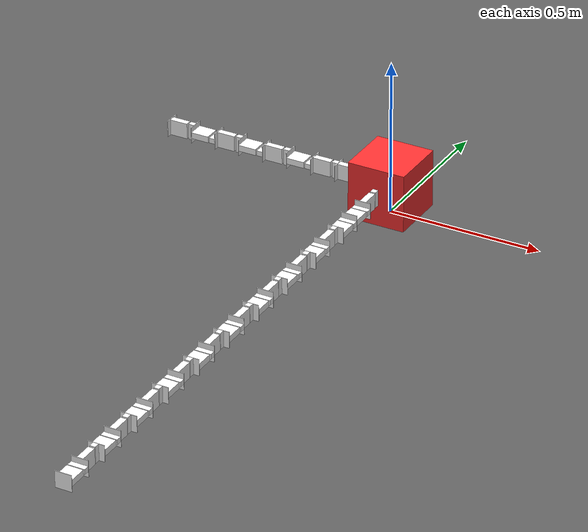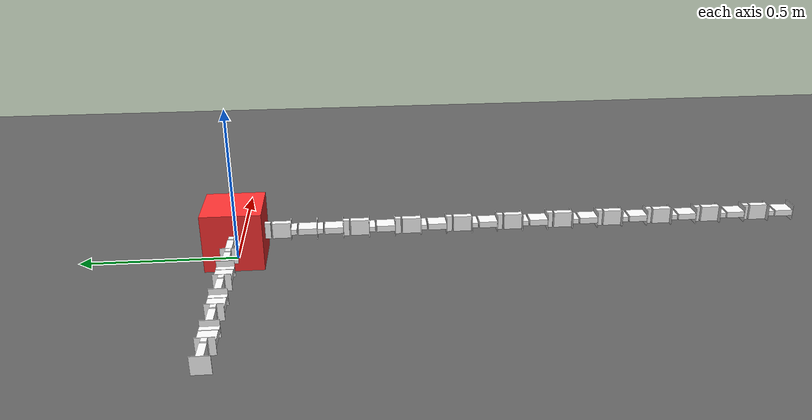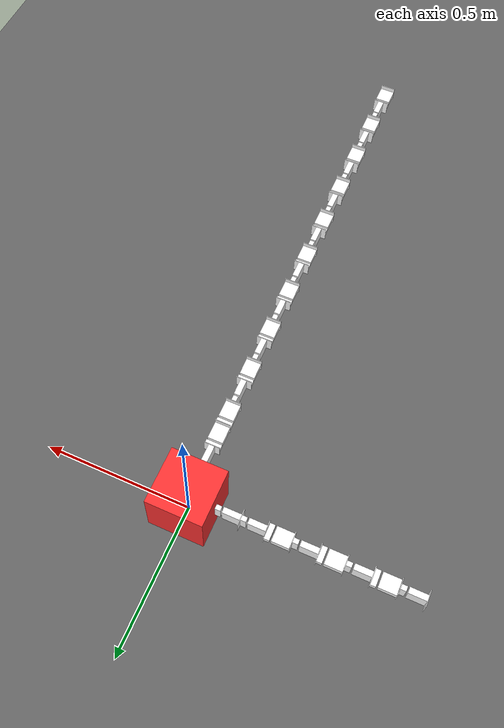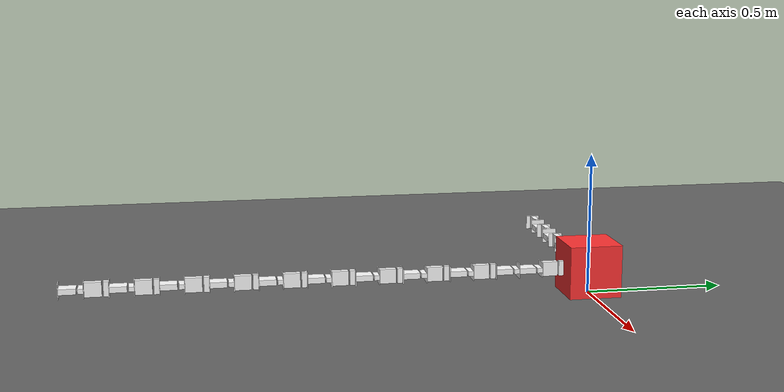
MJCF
<mujoco model="scene">
  <compiler angle="radian" autolimits="true"/>
  <option timestep="0.001" integrator="RK4"/>
  <visual>
    <headlight active="0"/>
  </visual>
  <statistic meansize="0.0570967" extent="2.88799" center="0 -0.443997 0"/>
  <default class="main">
    <default class="/"/>
    <default class="mbs0/"/>
    <default class="mbs1/"/>
  </default>
  <asset>
    <material name="heightmap_0_material" class="/" rgba="0.392157 0.392157 0.392157 1"/>
    <material name="mbs1/geom_mbs1_geom0_material" class="mbs1/" rgba="1 0.196078 0.196078 1"/>
    <material name="mbs1/geom_mbs1_geom1_material" class="mbs1/"/>
    <material name="mbs1/geom_mbs1_geom2_material" class="mbs1/"/>
    <material name="mbs1/geom_mbs1_link0_geom0_material" class="mbs1/"/>
    <material name="mbs1/geom_mbs1_link0_geom1_material" class="mbs1/"/>
    <material name="mbs1/geom_mbs1_link0_geom2_material" class="mbs1/"/>
    <material name="mbs1/geom_mbs1_link0_link1_geom0_material" class="mbs1/"/>
    <material name="mbs1/geom_mbs1_link0_link1_geom1_material" class="mbs1/"/>
    <material name="mbs1/geom_mbs1_link0_link1_geom2_material" class="mbs1/"/>
    <material name="mbs1/geom_mbs1_link0_link1_link1_geom0_material" class="mbs1/"/>
    <material name="mbs1/geom_mbs1_link0_link1_link1_geom1_material" class="mbs1/"/>
    <material name="mbs1/geom_mbs1_link0_link1_link1_geom2_material" class="mbs1/"/>
    <material name="mbs1/geom_mbs1_link0_link1_link1_link1_geom0_material" class="mbs1/"/>
    <material name="mbs1/geom_mbs1_link0_link1_link1_link1_geom1_material" class="mbs1/"/>
    <material name="mbs1/geom_mbs1_link0_link1_link1_link1_geom2_material" class="mbs1/"/>
    <material name="mbs1/geom_mbs1_link0_link1_link1_link1_link1_geom0_material" class="mbs1/"/>
    <material name="mbs1/geom_mbs1_link0_link1_link1_link1_link1_geom1_material" class="mbs1/"/>
    <material name="mbs1/geom_mbs1_link0_link1_link1_link1_link1_geom2_material" class="mbs1/"/>
    <material name="mbs1/geom_mbs1_link0_link1_link1_link1_link1_link1_geom0_material" class="mbs1/"/>
    <material name="mbs1/geom_mbs1_link0_link1_link1_link1_link1_link1_geom1_material" class="mbs1/"/>
    <material name="mbs1/geom_mbs1_link0_link1_link1_link1_link1_link1_geom2_material" class="mbs1/"/>
    <material name="mbs1/geom_mbs1_link0_link1_link1_link1_link1_link1_link1_geom0_material" class="mbs1/"/>
    <material name="mbs1/geom_mbs1_link0_link1_link1_link1_link1_link1_link1_geom1_material" class="mbs1/"/>
    <material name="mbs1/geom_mbs1_link0_link1_link1_link1_link1_link1_link1_geom2_material" class="mbs1/"/>
    <material name="mbs1/geom_mbs1_link0_link1_link1_link1_link1_link1_link1_link1_geom0_material" class="mbs1/"/>
    <material name="mbs1/geom_mbs1_link0_link1_link1_link1_link1_link1_link1_link1_geom1_material" class="mbs1/"/>
    <material name="mbs1/geom_mbs1_link1_geom0_material" class="mbs1/"/>
    <material name="mbs1/geom_mbs1_link1_geom1_material" class="mbs1/"/>
    <material name="mbs1/geom_mbs1_link1_geom2_material" class="mbs1/"/>
    <material name="mbs1/geom_mbs1_link1_link1_geom0_material" class="mbs1/"/>
    <material name="mbs1/geom_mbs1_link1_link1_geom1_material" class="mbs1/"/>
    <material name="mbs1/geom_mbs1_link1_link1_geom2_material" class="mbs1/"/>
    <material name="mbs1/geom_mbs1_link1_link1_link1_geom0_material" class="mbs1/"/>
    <material name="mbs1/geom_mbs1_link1_link1_link1_geom1_material" class="mbs1/"/>
    <material name="mbs1/geom_mbs1_link1_link1_link1_geom2_material" class="mbs1/"/>
    <material name="mbs1/geom_mbs1_link1_link1_link1_link1_geom0_material" class="mbs1/"/>
    <material name="mbs1/geom_mbs1_link1_link1_link1_link1_geom1_material" class="mbs1/"/>
    <material name="mbs1/geom_mbs1_link1_link1_link1_link1_geom2_material" class="mbs1/"/>
    <material name="mbs1/geom_mbs1_link1_link1_link1_link1_link1_geom0_material" class="mbs1/"/>
    <material name="mbs1/geom_mbs1_link1_link1_link1_link1_link1_geom1_material" class="mbs1/"/>
    <material name="mbs1/geom_mbs1_link1_link1_link1_link1_link1_geom2_material" class="mbs1/"/>
    <material name="mbs1/geom_mbs1_link1_link1_link1_link1_link1_link1_geom0_material" class="mbs1/"/>
    <material name="mbs1/geom_mbs1_link1_link1_link1_link1_link1_link1_geom1_material" class="mbs1/"/>
    <material name="mbs1/geom_mbs1_link1_link1_link1_link1_link1_link1_geom2_material" class="mbs1/"/>
    <material name="mbs1/geom_mbs1_link1_link1_link1_link1_link1_link1_link1_geom0_material" class="mbs1/"/>
    <material name="mbs1/geom_mbs1_link1_link1_link1_link1_link1_link1_link1_geom1_material" class="mbs1/"/>
    <material name="mbs1/geom_mbs1_link1_link1_link1_link1_link1_link1_link1_geom2_material" class="mbs1/"/>
    <material name="mbs1/geom_mbs1_link1_link1_link1_link1_link1_link1_link1_link1_geom0_material" class="mbs1/"/>
    <material name="mbs1/geom_mbs1_link1_link1_link1_link1_link1_link1_link1_link1_geom1_material" class="mbs1/"/>
    <material name="mbs1/geom_mbs1_link1_link1_link1_link1_link1_link1_link1_link1_geom2_material" class="mbs1/"/>
    <material name="mbs1/geom_mbs1_link1_link1_link1_link1_link1_link1_link1_link1_link1_geom0_material" class="mbs1/"/>
    <material name="mbs1/geom_mbs1_link1_link1_link1_link1_link1_link1_link1_link1_link1_geom1_material" class="mbs1/"/>
    <material name="mbs1/geom_mbs1_link1_link1_link1_link1_link1_link1_link1_link1_link1_geom2_material" class="mbs1/"/>
    <material name="mbs1/geom_mbs1_link1_link1_link1_link1_link1_link1_link1_link1_link1_link1_geom0_material" class="mbs1/"/>
    <material name="mbs1/geom_mbs1_link1_link1_link1_link1_link1_link1_link1_link1_link1_link1_geom1_material" class="mbs1/"/>
    <material name="mbs1/geom_mbs1_link1_link1_link1_link1_link1_link1_link1_link1_link1_link1_geom2_material" class="mbs1/"/>
    <material name="mbs1/geom_mbs1_link1_link1_link1_link1_link1_link1_link1_link1_link1_link1_link1_geom0_material" class="mbs1/"/>
    <material name="mbs1/geom_mbs1_link1_link1_link1_link1_link1_link1_link1_link1_link1_link1_link1_geom1_material" class="mbs1/"/>
    <material name="mbs1/geom_mbs1_link1_link1_link1_link1_link1_link1_link1_link1_link1_link1_link1_geom2_material" class="mbs1/"/>
    <material name="mbs1/geom_mbs1_link1_link1_link1_link1_link1_link1_link1_link1_link1_link1_link1_link1_geom0_material" class="mbs1/"/>
    <material name="mbs1/geom_mbs1_link1_link1_link1_link1_link1_link1_link1_link1_link1_link1_link1_link1_geom1_material" class="mbs1/"/>
    <material name="mbs1/geom_mbs1_link1_link1_link1_link1_link1_link1_link1_link1_link1_link1_link1_link1_geom2_material" class="mbs1/"/>
    <material name="mbs1/geom_mbs1_link1_link1_link1_link1_link1_link1_link1_link1_link1_link1_link1_link1_link1_geom0_material" class="mbs1/"/>
    <material name="mbs1/geom_mbs1_link1_link1_link1_link1_link1_link1_link1_link1_link1_link1_link1_link1_link1_geom1_material" class="mbs1/"/>
    <material name="mbs1/geom_mbs1_link1_link1_link1_link1_link1_link1_link1_link1_link1_link1_link1_link1_link1_geom2_material" class="mbs1/"/>
    <material name="mbs1/geom_mbs1_link1_link1_link1_link1_link1_link1_link1_link1_link1_link1_link1_link1_link1_link1_geom0_material" class="mbs1/"/>
    <material name="mbs1/geom_mbs1_link1_link1_link1_link1_link1_link1_link1_link1_link1_link1_link1_link1_link1_link1_geom1_material" class="mbs1/"/>
    <material name="mbs1/geom_mbs1_link1_link1_link1_link1_link1_link1_link1_link1_link1_link1_link1_link1_link1_link1_geom2_material" class="mbs1/"/>
    <material name="mbs1/geom_mbs1_link1_link1_link1_link1_link1_link1_link1_link1_link1_link1_link1_link1_link1_link1_link1_geom0_material" class="mbs1/"/>
    <material name="mbs1/geom_mbs1_link1_link1_link1_link1_link1_link1_link1_link1_link1_link1_link1_link1_link1_link1_link1_geom1_material" class="mbs1/"/>
    <material name="mbs1/geom_mbs1_link1_link1_link1_link1_link1_link1_link1_link1_link1_link1_link1_link1_link1_link1_link1_geom2_material" class="mbs1/"/>
    <material name="mbs1/geom_mbs1_link1_link1_link1_link1_link1_link1_link1_link1_link1_link1_link1_link1_link1_link1_link1_link1_geom0_material" class="mbs1/"/>
    <material name="mbs1/geom_mbs1_link1_link1_link1_link1_link1_link1_link1_link1_link1_link1_link1_link1_link1_link1_link1_link1_geom1_material" class="mbs1/"/>
    <material name="mbs1/geom_mbs1_link1_link1_link1_link1_link1_link1_link1_link1_link1_link1_link1_link1_link1_link1_link1_link1_geom2_material" class="mbs1/"/>
    <material name="mbs1/geom_mbs1_link1_link1_link1_link1_link1_link1_link1_link1_link1_link1_link1_link1_link1_link1_link1_link1_link1_geom0_material" class="mbs1/"/>
    <material name="mbs1/geom_mbs1_link1_link1_link1_link1_link1_link1_link1_link1_link1_link1_link1_link1_link1_link1_link1_link1_link1_geom1_material" class="mbs1/"/>
    <material name="mbs1/geom_mbs1_link1_link1_link1_link1_link1_link1_link1_link1_link1_link1_link1_link1_link1_link1_link1_link1_link1_geom2_material" class="mbs1/"/>
    <material name="mbs1/geom_mbs1_link1_link1_link1_link1_link1_link1_link1_link1_link1_link1_link1_link1_link1_link1_link1_link1_link1_link1_geom0_material" class="mbs1/"/>
    <material name="mbs1/geom_mbs1_link1_link1_link1_link1_link1_link1_link1_link1_link1_link1_link1_link1_link1_link1_link1_link1_link1_link1_geom1_material" class="mbs1/"/>
    <material name="mbs1/geom_mbs1_link1_link1_link1_link1_link1_link1_link1_link1_link1_link1_link1_link1_link1_link1_link1_link1_link1_link1_geom2_material" class="mbs1/"/>
    <material name="mbs1/geom_mbs1_link1_link1_link1_link1_link1_link1_link1_link1_link1_link1_link1_link1_link1_link1_link1_link1_link1_link1_link1_geom0_material" class="mbs1/"/>
    <material name="mbs1/geom_mbs1_link1_link1_link1_link1_link1_link1_link1_link1_link1_link1_link1_link1_link1_link1_link1_link1_link1_link1_link1_geom1_material" class="mbs1/"/>
    <material name="mbs1/geom_mbs1_link1_link1_link1_link1_link1_link1_link1_link1_link1_link1_link1_link1_link1_link1_link1_link1_link1_link1_link1_geom2_material" class="mbs1/"/>
    <material name="mbs1/geom_mbs1_link1_link1_link1_link1_link1_link1_link1_link1_link1_link1_link1_link1_link1_link1_link1_link1_link1_link1_link1_link1_geom0_material" class="mbs1/"/>
    <material name="mbs1/geom_mbs1_link1_link1_link1_link1_link1_link1_link1_link1_link1_link1_link1_link1_link1_link1_link1_link1_link1_link1_link1_link1_geom1_material" class="mbs1/"/>
    <material name="mbs1/geom_mbs1_link1_link1_link1_link1_link1_link1_link1_link1_link1_link1_link1_link1_link1_link1_link1_link1_link1_link1_link1_link1_geom2_material" class="mbs1/"/>
    <material name="mbs1/geom_mbs1_link1_link1_link1_link1_link1_link1_link1_link1_link1_link1_link1_link1_link1_link1_link1_link1_link1_link1_link1_link1_link1_geom0_material" class="mbs1/"/>
    <material name="mbs1/geom_mbs1_link1_link1_link1_link1_link1_link1_link1_link1_link1_link1_link1_link1_link1_link1_link1_link1_link1_link1_link1_link1_link1_geom1_material" class="mbs1/"/>
  </asset>
  <worldbody>
    <geom name="//unnamed_geom_0" class="/" size="10 10 1" quat="0 0 0 1" type="plane" material="heightmap_0_material"/>
    <light name="//unnamed_light_0" class="/" pos="0 0 100" dir="0 0 -1" directional="true" castshadow="false" ambient="0.5 0.5 0.5"/>
    <body name="mbs0/" quat="0 0 0 1"/>
    <body name="mbs1/" pos="0 0 0.0943294" quat="0 0 0 1">
      <joint name="mbs1/" type="free"/>
      <geom name="mbs1/mbs1_geom0" class="mbs1/" size="0.0943294 0.0943294 0.0943294" type="box" material="mbs1/geom_mbs1_geom0_material"/>
      <geom name="mbs1/mbs1_geom1" class="mbs1/" size="0.009 0.0265 0.00829455" pos="0.103329 0 0" quat="0.707107 0.707107 0 0" type="box" material="mbs1/geom_mbs1_geom1_material"/>
      <geom name="mbs1/mbs1_geom2" class="mbs1/" size="0.009 0.0265 0.00829455" pos="0 0.103329 0" quat="0.5 0.5 0.5 0.5" type="box" material="mbs1/geom_mbs1_geom2_material"/>
      <site name="mbs1/mbs1_site_imu_0" class="mbs1/" pos="0 0 0" quat="0 0 0 1"/>
      <body name="mbs1/mbs1_link0" pos="0.128854 0 0" quat="0.707107 0.707107 0 0">
        <inertial pos="0.0321864 0 0" quat="0 0.707107 0 0.707107" mass="0.09932" diaginertia="6.82647e-05 5.40817e-05 3.05023e-05"/>
        <joint name="mbs1/mbs1_joint0" class="mbs1/" pos="0 0 0" axis="0 1 0" range="-1.0472 1.0472" armature="0.002"/>
        <geom name="mbs1/mbs1_link0_geom0" class="mbs1/" size="0.02915 0.0256 0.01" pos="0.018 0 0" type="box" material="mbs1/geom_mbs1_link0_geom0_material"/>
        <geom name="mbs1/mbs1_link0_geom1" class="mbs1/" size="0.001 0.0265 0.0265" pos="0.04815 0 0" type="box" material="mbs1/geom_mbs1_link0_geom1_material"/>
        <geom name="mbs1/mbs1_link0_geom2" class="mbs1/" size="0.009 0.0265 0.00829455" pos="0.05815 0 0" type="box" material="mbs1/geom_mbs1_link0_geom2_material"/>
        <body name="mbs1/mbs1_link0_link1" pos="0.083675 0 0">
          <inertial pos="0.0321864 0 0" quat="0 0.707107 0 0.707107" mass="0.09932" diaginertia="6.82647e-05 5.74613e-05 2.71227e-05"/>
          <joint name="mbs1/mbs1_link0_joint1" class="mbs1/" pos="0 0 0" axis="0 1 0" range="-1.0472 1.0472" armature="0.002"/>
          <geom name="mbs1/mbs1_link0_link1_geom0" class="mbs1/" size="0.02915 0.0256 0.01" pos="0.018 0 0" type="box" material="mbs1/geom_mbs1_link0_link1_geom0_material"/>
          <geom name="mbs1/mbs1_link0_link1_geom1" class="mbs1/" size="0.001 0.0265 0.0265" pos="0.04815 0 0" type="box" material="mbs1/geom_mbs1_link0_link1_geom1_material"/>
          <geom name="mbs1/mbs1_link0_link1_geom2" class="mbs1/" size="0.009 0.0265 0.00829455" pos="0.05815 0 0" quat="0.707107 0.707107 0 0" type="box" material="mbs1/geom_mbs1_link0_link1_geom2_material"/>
          <body name="mbs1/mbs1_link0_link1_link1" pos="0.083675 0 0" quat="0.707107 0.707107 0 0">
            <inertial pos="0.0321864 0 0" quat="0 0.707107 0 0.707107" mass="0.09932" diaginertia="6.82647e-05 5.74613e-05 2.71227e-05"/>
            <joint name="mbs1/mbs1_link0_link1_joint1" class="mbs1/" pos="0 0 0" axis="0 1 0" range="-1.0472 1.0472" armature="0.002"/>
            <geom name="mbs1/mbs1_link0_link1_link1_geom0" class="mbs1/" size="0.02915 0.0256 0.01" pos="0.018 0 0" type="box" material="mbs1/geom_mbs1_link0_link1_link1_geom0_material"/>
            <geom name="mbs1/mbs1_link0_link1_link1_geom1" class="mbs1/" size="0.001 0.0265 0.0265" pos="0.04815 0 0" type="box" material="mbs1/geom_mbs1_link0_link1_link1_geom1_material"/>
            <geom name="mbs1/mbs1_link0_link1_link1_geom2" class="mbs1/" size="0.009 0.0265 0.00829455" pos="0.05815 0 0" quat="0.707107 0.707107 0 0" type="box" material="mbs1/geom_mbs1_link0_link1_link1_geom2_material"/>
            <body name="mbs1/mbs1_link0_link1_link1_link1" pos="0.083675 0 0" quat="0.707107 0.707107 0 0">
              <inertial pos="0.0321864 0 0" quat="0 0.707107 0 0.707107" mass="0.09932" diaginertia="6.82647e-05 5.74613e-05 2.71227e-05"/>
              <joint name="mbs1/mbs1_link0_link1_link1_joint1" class="mbs1/" pos="0 0 0" axis="0 1 0" range="-1.0472 1.0472" armature="0.002"/>
              <geom name="mbs1/mbs1_link0_link1_link1_link1_geom0" class="mbs1/" size="0.02915 0.0256 0.01" pos="0.018 0 0" type="box" material="mbs1/geom_mbs1_link0_link1_link1_link1_geom0_material"/>
              <geom name="mbs1/mbs1_link0_link1_link1_link1_geom1" class="mbs1/" size="0.001 0.0265 0.0265" pos="0.04815 0 0" type="box" material="mbs1/geom_mbs1_link0_link1_link1_link1_geom1_material"/>
              <geom name="mbs1/mbs1_link0_link1_link1_link1_geom2" class="mbs1/" size="0.009 0.0265 0.00829455" pos="0.05815 0 0" quat="0.707107 0.707107 0 0" type="box" material="mbs1/geom_mbs1_link0_link1_link1_link1_geom2_material"/>
              <body name="mbs1/mbs1_link0_link1_link1_link1_link1" pos="0.083675 0 0" quat="0.707107 0.707107 0 0">
                <inertial pos="0.0321864 0 0" quat="0 0.707107 0 0.707107" mass="0.09932" diaginertia="6.82647e-05 5.74613e-05 2.71227e-05"/>
                <joint name="mbs1/mbs1_link0_link1_link1_link1_joint1" class="mbs1/" pos="0 0 0" axis="0 1 0" range="-1.0472 1.0472" armature="0.002"/>
                <geom name="mbs1/mbs1_link0_link1_link1_link1_link1_geom0" class="mbs1/" size="0.02915 0.0256 0.01" pos="0.018 0 0" type="box" material="mbs1/geom_mbs1_link0_link1_link1_link1_link1_geom0_material"/>
                <geom name="mbs1/mbs1_link0_link1_link1_link1_link1_geom1" class="mbs1/" size="0.001 0.0265 0.0265" pos="0.04815 0 0" type="box" material="mbs1/geom_mbs1_link0_link1_link1_link1_link1_geom1_material"/>
                <geom name="mbs1/mbs1_link0_link1_link1_link1_link1_geom2" class="mbs1/" size="0.009 0.0265 0.00829455" pos="0.05815 0 0" quat="0.707107 0.707107 0 0" type="box" material="mbs1/geom_mbs1_link0_link1_link1_link1_link1_geom2_material"/>
                <body name="mbs1/mbs1_link0_link1_link1_link1_link1_link1" pos="0.083675 0 0" quat="0.707107 0.707107 0 0">
                  <inertial pos="0.0321864 0 0" quat="0 0.707107 0 0.707107" mass="0.09932" diaginertia="6.82647e-05 5.74613e-05 2.71227e-05"/>
                  <joint name="mbs1/mbs1_link0_link1_link1_link1_link1_joint1" class="mbs1/" pos="0 0 0" axis="0 1 0" range="-1.0472 1.0472" armature="0.002"/>
                  <geom name="mbs1/mbs1_link0_link1_link1_link1_link1_link1_geom0" class="mbs1/" size="0.02915 0.0256 0.01" pos="0.018 0 0" type="box" material="mbs1/geom_mbs1_link0_link1_link1_link1_link1_link1_geom0_material"/>
                  <geom name="mbs1/mbs1_link0_link1_link1_link1_link1_link1_geom1" class="mbs1/" size="0.001 0.0265 0.0265" pos="0.04815 0 0" type="box" material="mbs1/geom_mbs1_link0_link1_link1_link1_link1_link1_geom1_material"/>
                  <geom name="mbs1/mbs1_link0_link1_link1_link1_link1_link1_geom2" class="mbs1/" size="0.009 0.0265 0.00829455" pos="0.05815 0 0" quat="0.707107 0.707107 0 0" type="box" material="mbs1/geom_mbs1_link0_link1_link1_link1_link1_link1_geom2_material"/>
                  <body name="mbs1/mbs1_link0_link1_link1_link1_link1_link1_link1" pos="0.083675 0 0" quat="0.707107 0.707107 0 0">
                    <inertial pos="0.0321864 0 0" quat="0 0.707107 0 0.707107" mass="0.09932" diaginertia="6.82647e-05 5.74613e-05 2.71227e-05"/>
                    <joint name="mbs1/mbs1_link0_link1_link1_link1_link1_link1_joint1" class="mbs1/" pos="0 0 0" axis="0 1 0" range="-1.0472 1.0472" armature="0.002"/>
                    <geom name="mbs1/mbs1_link0_link1_link1_link1_link1_link1_link1_geom0" class="mbs1/" size="0.02915 0.0256 0.01" pos="0.018 0 0" type="box" material="mbs1/geom_mbs1_link0_link1_link1_link1_link1_link1_link1_geom0_material"/>
                    <geom name="mbs1/mbs1_link0_link1_link1_link1_link1_link1_link1_geom1" class="mbs1/" size="0.001 0.0265 0.0265" pos="0.04815 0 0" type="box" material="mbs1/geom_mbs1_link0_link1_link1_link1_link1_link1_link1_geom1_material"/>
                    <geom name="mbs1/mbs1_link0_link1_link1_link1_link1_link1_link1_geom2" class="mbs1/" size="0.009 0.0265 0.00829455" pos="0.05815 0 0" quat="0.707107 0.707107 0 0" type="box" material="mbs1/geom_mbs1_link0_link1_link1_link1_link1_link1_link1_geom2_material"/>
                    <body name="mbs1/mbs1_link0_link1_link1_link1_link1_link1_link1_link1" pos="0.083675 0 0" quat="0.707107 0.707107 0 0">
                      <inertial pos="0.0270813 0 0" quat="0 0.707107 0 0.707107" mass="0.083" diaginertia="5.08392e-05 4.01022e-05 2.63078e-05"/>
                      <joint name="mbs1/mbs1_link0_link1_link1_link1_link1_link1_link1_joint1" class="mbs1/" pos="0 0 0" axis="0 1 0" range="-1.0472 1.0472" armature="0.002"/>
                      <geom name="mbs1/mbs1_link0_link1_link1_link1_link1_link1_link1_link1_geom0" class="mbs1/" size="0.02915 0.0256 0.01" pos="0.018 0 0" type="box" material="mbs1/geom_mbs1_link0_link1_link1_link1_link1_link1_link1_link1_geom0_material"/>
                      <geom name="mbs1/mbs1_link0_link1_link1_link1_link1_link1_link1_link1_geom1" class="mbs1/" size="0.001 0.0265 0.0265" pos="0.04815 0 0" type="box" material="mbs1/geom_mbs1_link0_link1_link1_link1_link1_link1_link1_link1_geom1_material"/>
                    </body>
                  </body>
                </body>
              </body>
            </body>
          </body>
        </body>
      </body>
      <body name="mbs1/mbs1_link1" pos="0 0.128854 0" quat="0.5 0.5 0.5 0.5">
        <inertial pos="0.0321864 0 0" quat="0 0.707107 0 0.707107" mass="0.09932" diaginertia="6.82647e-05 5.74613e-05 2.71227e-05"/>
        <joint name="mbs1/mbs1_joint1" class="mbs1/" pos="0 0 0" axis="0 1 0" range="-1.0472 1.0472" armature="0.002"/>
        <geom name="mbs1/mbs1_link1_geom0" class="mbs1/" size="0.02915 0.0256 0.01" pos="0.018 0 0" type="box" material="mbs1/geom_mbs1_link1_geom0_material"/>
        <geom name="mbs1/mbs1_link1_geom1" class="mbs1/" size="0.001 0.0265 0.0265" pos="0.04815 0 0" type="box" material="mbs1/geom_mbs1_link1_geom1_material"/>
        <geom name="mbs1/mbs1_link1_geom2" class="mbs1/" size="0.009 0.0265 0.00829455" pos="0.05815 0 0" quat="0.707107 0.707107 0 0" type="box" material="mbs1/geom_mbs1_link1_geom2_material"/>
        <body name="mbs1/mbs1_link1_link1" pos="0.083675 0 0" quat="0.707107 0.707107 0 0">
          <inertial pos="0.0321864 0 0" quat="0 0.707107 0 0.707107" mass="0.09932" diaginertia="6.82647e-05 5.40817e-05 3.05023e-05"/>
          <joint name="mbs1/mbs1_link1_joint1" class="mbs1/" pos="0 0 0" axis="0 1 0" range="-1.0472 1.0472" armature="0.002"/>
          <geom name="mbs1/mbs1_link1_link1_geom0" class="mbs1/" size="0.02915 0.0256 0.01" pos="0.018 0 0" type="box" material="mbs1/geom_mbs1_link1_link1_geom0_material"/>
          <geom name="mbs1/mbs1_link1_link1_geom1" class="mbs1/" size="0.001 0.0265 0.0265" pos="0.04815 0 0" type="box" material="mbs1/geom_mbs1_link1_link1_geom1_material"/>
          <geom name="mbs1/mbs1_link1_link1_geom2" class="mbs1/" size="0.009 0.0265 0.00829455" pos="0.05815 0 0" type="box" material="mbs1/geom_mbs1_link1_link1_geom2_material"/>
          <body name="mbs1/mbs1_link1_link1_link1" pos="0.083675 0 0">
            <inertial pos="0.0321864 0 0" quat="0 0.707107 0 0.707107" mass="0.09932" diaginertia="6.82647e-05 5.74613e-05 2.71227e-05"/>
            <joint name="mbs1/mbs1_link1_link1_joint1" class="mbs1/" pos="0 0 0" axis="0 1 0" range="-1.0472 1.0472" armature="0.002"/>
            <geom name="mbs1/mbs1_link1_link1_link1_geom0" class="mbs1/" size="0.02915 0.0256 0.01" pos="0.018 0 0" type="box" material="mbs1/geom_mbs1_link1_link1_link1_geom0_material"/>
            <geom name="mbs1/mbs1_link1_link1_link1_geom1" class="mbs1/" size="0.001 0.0265 0.0265" pos="0.04815 0 0" type="box" material="mbs1/geom_mbs1_link1_link1_link1_geom1_material"/>
            <geom name="mbs1/mbs1_link1_link1_link1_geom2" class="mbs1/" size="0.009 0.0265 0.00829455" pos="0.05815 0 0" quat="0.707107 0.707107 0 0" type="box" material="mbs1/geom_mbs1_link1_link1_link1_geom2_material"/>
            <body name="mbs1/mbs1_link1_link1_link1_link1" pos="0.083675 0 0" quat="0.707107 0.707107 0 0">
              <inertial pos="0.0321864 0 0" quat="0 0.707107 0 0.707107" mass="0.09932" diaginertia="6.82647e-05 5.74613e-05 2.71227e-05"/>
              <joint name="mbs1/mbs1_link1_link1_link1_joint1" class="mbs1/" pos="0 0 0" axis="0 1 0" range="-1.0472 1.0472" armature="0.002"/>
              <geom name="mbs1/mbs1_link1_link1_link1_link1_geom0" class="mbs1/" size="0.02915 0.0256 0.01" pos="0.018 0 0" type="box" material="mbs1/geom_mbs1_link1_link1_link1_link1_geom0_material"/>
              <geom name="mbs1/mbs1_link1_link1_link1_link1_geom1" class="mbs1/" size="0.001 0.0265 0.0265" pos="0.04815 0 0" type="box" material="mbs1/geom_mbs1_link1_link1_link1_link1_geom1_material"/>
              <geom name="mbs1/mbs1_link1_link1_link1_link1_geom2" class="mbs1/" size="0.009 0.0265 0.00829455" pos="0.05815 0 0" quat="0.707107 0.707107 0 0" type="box" material="mbs1/geom_mbs1_link1_link1_link1_link1_geom2_material"/>
              <body name="mbs1/mbs1_link1_link1_link1_link1_link1" pos="0.083675 0 0" quat="0.707107 0.707107 0 0">
                <inertial pos="0.0321864 0 0" quat="0 0.707107 0 0.707107" mass="0.09932" diaginertia="6.82647e-05 5.74613e-05 2.71227e-05"/>
                <joint name="mbs1/mbs1_link1_link1_link1_link1_joint1" class="mbs1/" pos="0 0 0" axis="0 1 0" range="-1.0472 1.0472" armature="0.002"/>
                <geom name="mbs1/mbs1_link1_link1_link1_link1_link1_geom0" class="mbs1/" size="0.02915 0.0256 0.01" pos="0.018 0 0" type="box" material="mbs1/geom_mbs1_link1_link1_link1_link1_link1_geom0_material"/>
                <geom name="mbs1/mbs1_link1_link1_link1_link1_link1_geom1" class="mbs1/" size="0.001 0.0265 0.0265" pos="0.04815 0 0" type="box" material="mbs1/geom_mbs1_link1_link1_link1_link1_link1_geom1_material"/>
                <geom name="mbs1/mbs1_link1_link1_link1_link1_link1_geom2" class="mbs1/" size="0.009 0.0265 0.00829455" pos="0.05815 0 0" quat="0.707107 0.707107 0 0" type="box" material="mbs1/geom_mbs1_link1_link1_link1_link1_link1_geom2_material"/>
                <body name="mbs1/mbs1_link1_link1_link1_link1_link1_link1" pos="0.083675 0 0" quat="0.707107 0.707107 0 0">
                  <inertial pos="0.0321864 0 0" quat="0 0.707107 0 0.707107" mass="0.09932" diaginertia="6.82647e-05 5.74613e-05 2.71227e-05"/>
                  <joint name="mbs1/mbs1_link1_link1_link1_link1_link1_joint1" class="mbs1/" pos="0 0 0" axis="0 1 0" range="-1.0472 1.0472" armature="0.002"/>
                  <geom name="mbs1/mbs1_link1_link1_link1_link1_link1_link1_geom0" class="mbs1/" size="0.02915 0.0256 0.01" pos="0.018 0 0" type="box" material="mbs1/geom_mbs1_link1_link1_link1_link1_link1_link1_geom0_material"/>
                  <geom name="mbs1/mbs1_link1_link1_link1_link1_link1_link1_geom1" class="mbs1/" size="0.001 0.0265 0.0265" pos="0.04815 0 0" type="box" material="mbs1/geom_mbs1_link1_link1_link1_link1_link1_link1_geom1_material"/>
                  <geom name="mbs1/mbs1_link1_link1_link1_link1_link1_link1_geom2" class="mbs1/" size="0.009 0.0265 0.00829455" pos="0.05815 0 0" quat="0.707107 0.707107 0 0" type="box" material="mbs1/geom_mbs1_link1_link1_link1_link1_link1_link1_geom2_material"/>
                  <body name="mbs1/mbs1_link1_link1_link1_link1_link1_link1_link1" pos="0.083675 0 0" quat="0.707107 0.707107 0 0">
                    <inertial pos="0.0321864 0 0" quat="0 0.707107 0 0.707107" mass="0.09932" diaginertia="6.82647e-05 5.74613e-05 2.71227e-05"/>
                    <joint name="mbs1/mbs1_link1_link1_link1_link1_link1_link1_joint1" class="mbs1/" pos="0 0 0" axis="0 1 0" range="-1.0472 1.0472" armature="0.002"/>
                    <geom name="mbs1/mbs1_link1_link1_link1_link1_link1_link1_link1_geom0" class="mbs1/" size="0.02915 0.0256 0.01" pos="0.018 0 0" type="box" material="mbs1/geom_mbs1_link1_link1_link1_link1_link1_link1_link1_geom0_material"/>
                    <geom name="mbs1/mbs1_link1_link1_link1_link1_link1_link1_link1_geom1" class="mbs1/" size="0.001 0.0265 0.0265" pos="0.04815 0 0" type="box" material="mbs1/geom_mbs1_link1_link1_link1_link1_link1_link1_link1_geom1_material"/>
                    <geom name="mbs1/mbs1_link1_link1_link1_link1_link1_link1_link1_geom2" class="mbs1/" size="0.009 0.0265 0.00829455" pos="0.05815 0 0" quat="0.707107 0.707107 0 0" type="box" material="mbs1/geom_mbs1_link1_link1_link1_link1_link1_link1_link1_geom2_material"/>
                    <body name="mbs1/mbs1_link1_link1_link1_link1_link1_link1_link1_link1" pos="0.083675 0 0" quat="0.707107 0.707107 0 0">
                      <inertial pos="0.0321864 0 0" quat="0 0.707107 0 0.707107" mass="0.09932" diaginertia="6.82647e-05 5.74613e-05 2.71227e-05"/>
                      <joint name="mbs1/mbs1_link1_link1_link1_link1_link1_link1_link1_joint1" class="mbs1/" pos="0 0 0" axis="0 1 0" range="-1.0472 1.0472" armature="0.002"/>
                      <geom name="mbs1/mbs1_link1_link1_link1_link1_link1_link1_link1_link1_geom0" class="mbs1/" size="0.02915 0.0256 0.01" pos="0.018 0 0" type="box" material="mbs1/geom_mbs1_link1_link1_link1_link1_link1_link1_link1_link1_geom0_material"/>
                      <geom name="mbs1/mbs1_link1_link1_link1_link1_link1_link1_link1_link1_geom1" class="mbs1/" size="0.001 0.0265 0.0265" pos="0.04815 0 0" type="box" material="mbs1/geom_mbs1_link1_link1_link1_link1_link1_link1_link1_link1_geom1_material"/>
                      <geom name="mbs1/mbs1_link1_link1_link1_link1_link1_link1_link1_link1_geom2" class="mbs1/" size="0.009 0.0265 0.00829455" pos="0.05815 0 0" quat="0.707107 0.707107 0 0" type="box" material="mbs1/geom_mbs1_link1_link1_link1_link1_link1_link1_link1_link1_geom2_material"/>
                      <body name="mbs1/mbs1_link1_link1_link1_link1_link1_link1_link1_link1_link1" pos="0.083675 0 0" quat="0.707107 0.707107 0 0">
                        <inertial pos="0.0321864 0 0" quat="0 0.707107 0 0.707107" mass="0.09932" diaginertia="6.82647e-05 5.74613e-05 2.71227e-05"/>
                        <joint name="mbs1/mbs1_link1_link1_link1_link1_link1_link1_link1_link1_joint1" class="mbs1/" pos="0 0 0" axis="0 1 0" range="-1.0472 1.0472" armature="0.002"/>
                        <geom name="mbs1/mbs1_link1_link1_link1_link1_link1_link1_link1_link1_link1_geom0" class="mbs1/" size="0.02915 0.0256 0.01" pos="0.018 0 0" type="box" material="mbs1/geom_mbs1_link1_link1_link1_link1_link1_link1_link1_link1_link1_geom0_material"/>
                        <geom name="mbs1/mbs1_link1_link1_link1_link1_link1_link1_link1_link1_link1_geom1" class="mbs1/" size="0.001 0.0265 0.0265" pos="0.04815 0 0" type="box" material="mbs1/geom_mbs1_link1_link1_link1_link1_link1_link1_link1_link1_link1_geom1_material"/>
                        <geom name="mbs1/mbs1_link1_link1_link1_link1_link1_link1_link1_link1_link1_geom2" class="mbs1/" size="0.009 0.0265 0.00829455" pos="0.05815 0 0" quat="0.707107 0.707107 0 0" type="box" material="mbs1/geom_mbs1_link1_link1_link1_link1_link1_link1_link1_link1_link1_geom2_material"/>
                        <body name="mbs1/mbs1_link1_link1_link1_link1_link1_link1_link1_link1_link1_link1" pos="0.083675 0 0" quat="0.707107 0.707107 0 0">
                          <inertial pos="0.0321864 0 0" quat="0 0.707107 0 0.707107" mass="0.09932" diaginertia="6.82647e-05 5.74613e-05 2.71227e-05"/>
                          <joint name="mbs1/mbs1_link1_link1_link1_link1_link1_link1_link1_link1_link1_joint1" class="mbs1/" pos="0 0 0" axis="0 1 0" range="-1.0472 1.0472" armature="0.002"/>
                          <geom name="mbs1/mbs1_link1_link1_link1_link1_link1_link1_link1_link1_link1_link1_geom0" class="mbs1/" size="0.02915 0.0256 0.01" pos="0.018 0 0" type="box" material="mbs1/geom_mbs1_link1_link1_link1_link1_link1_link1_link1_link1_link1_link1_geom0_material"/>
                          <geom name="mbs1/mbs1_link1_link1_link1_link1_link1_link1_link1_link1_link1_link1_geom1" class="mbs1/" size="0.001 0.0265 0.0265" pos="0.04815 0 0" type="box" material="mbs1/geom_mbs1_link1_link1_link1_link1_link1_link1_link1_link1_link1_link1_geom1_material"/>
                          <geom name="mbs1/mbs1_link1_link1_link1_link1_link1_link1_link1_link1_link1_link1_geom2" class="mbs1/" size="0.009 0.0265 0.00829455" pos="0.05815 0 0" quat="0.707107 0.707107 0 0" type="box" material="mbs1/geom_mbs1_link1_link1_link1_link1_link1_link1_link1_link1_link1_link1_geom2_material"/>
                          <body name="mbs1/mbs1_link1_link1_link1_link1_link1_link1_link1_link1_link1_link1_link1" pos="0.083675 0 0" quat="0.707107 0.707107 0 0">
                            <inertial pos="0.0321864 0 0" quat="0 0.707107 0 0.707107" mass="0.09932" diaginertia="6.82647e-05 5.74613e-05 2.71227e-05"/>
                            <joint name="mbs1/mbs1_link1_link1_link1_link1_link1_link1_link1_link1_link1_link1_joint1" class="mbs1/" pos="0 0 0" axis="0 1 0" range="-1.0472 1.0472" armature="0.002"/>
                            <geom name="mbs1/mbs1_link1_link1_link1_link1_link1_link1_link1_link1_link1_link1_link1_geom0" class="mbs1/" size="0.02915 0.0256 0.01" pos="0.018 0 0" type="box" material="mbs1/geom_mbs1_link1_link1_link1_link1_link1_link1_link1_link1_link1_link1_link1_geom0_material"/>
                            <geom name="mbs1/mbs1_link1_link1_link1_link1_link1_link1_link1_link1_link1_link1_link1_geom1" class="mbs1/" size="0.001 0.0265 0.0265" pos="0.04815 0 0" type="box" material="mbs1/geom_mbs1_link1_link1_link1_link1_link1_link1_link1_link1_link1_link1_link1_geom1_material"/>
                            <geom name="mbs1/mbs1_link1_link1_link1_link1_link1_link1_link1_link1_link1_link1_link1_geom2" class="mbs1/" size="0.009 0.0265 0.00829455" pos="0.05815 0 0" quat="0.707107 0.707107 0 0" type="box" material="mbs1/geom_mbs1_link1_link1_link1_link1_link1_link1_link1_link1_link1_link1_link1_geom2_material"/>
                            <body name="mbs1/mbs1_link1_link1_link1_link1_link1_link1_link1_link1_link1_link1_link1_link1" pos="0.083675 0 0" quat="0.707107 0.707107 0 0">
                              <inertial pos="0.0321864 0 0" quat="0 0.707107 0 0.707107" mass="0.09932" diaginertia="6.82647e-05 5.74613e-05 2.71227e-05"/>
                              <joint name="mbs1/mbs1_link1_link1_link1_link1_link1_link1_link1_link1_link1_link1_link1_joint1" class="mbs1/" pos="0 0 0" axis="0 1 0" range="-1.0472 1.0472" armature="0.002"/>
                              <geom name="mbs1/mbs1_link1_link1_link1_link1_link1_link1_link1_link1_link1_link1_link1_link1_geom0" class="mbs1/" size="0.02915 0.0256 0.01" pos="0.018 0 0" type="box" material="mbs1/geom_mbs1_link1_link1_link1_link1_link1_link1_link1_link1_link1_link1_link1_link1_geom0_material"/>
                              <geom name="mbs1/mbs1_link1_link1_link1_link1_link1_link1_link1_link1_link1_link1_link1_link1_geom1" class="mbs1/" size="0.001 0.0265 0.0265" pos="0.04815 0 0" type="box" material="mbs1/geom_mbs1_link1_link1_link1_link1_link1_link1_link1_link1_link1_link1_link1_link1_geom1_material"/>
                              <geom name="mbs1/mbs1_link1_link1_link1_link1_link1_link1_link1_link1_link1_link1_link1_link1_geom2" class="mbs1/" size="0.009 0.0265 0.00829455" pos="0.05815 0 0" quat="0.707107 0.707107 0 0" type="box" material="mbs1/geom_mbs1_link1_link1_link1_link1_link1_link1_link1_link1_link1_link1_link1_link1_geom2_material"/>
                              <body name="mbs1/mbs1_link1_link1_link1_link1_link1_link1_link1_link1_link1_link1_link1_link1_link1" pos="0.083675 0 0" quat="0.707107 0.707107 0 0">
                                <inertial pos="0.0321864 0 0" quat="0 0.707107 0 0.707107" mass="0.09932" diaginertia="6.82647e-05 5.74613e-05 2.71227e-05"/>
                                <joint name="mbs1/mbs1_link1_link1_link1_link1_link1_link1_link1_link1_link1_link1_link1_link1_joint1" class="mbs1/" pos="0 0 0" axis="0 1 0" range="-1.0472 1.0472" armature="0.002"/>
                                <geom name="mbs1/mbs1_link1_link1_link1_link1_link1_link1_link1_link1_link1_link1_link1_link1_link1_geom0" class="mbs1/" size="0.02915 0.0256 0.01" pos="0.018 0 0" type="box" material="mbs1/geom_mbs1_link1_link1_link1_link1_link1_link1_link1_link1_link1_link1_link1_link1_link1_geom0_material"/>
                                <geom name="mbs1/mbs1_link1_link1_link1_link1_link1_link1_link1_link1_link1_link1_link1_link1_link1_geom1" class="mbs1/" size="0.001 0.0265 0.0265" pos="0.04815 0 0" type="box" material="mbs1/geom_mbs1_link1_link1_link1_link1_link1_link1_link1_link1_link1_link1_link1_link1_link1_geom1_material"/>
                                <geom name="mbs1/mbs1_link1_link1_link1_link1_link1_link1_link1_link1_link1_link1_link1_link1_link1_geom2" class="mbs1/" size="0.009 0.0265 0.00829455" pos="0.05815 0 0" quat="0.707107 0.707107 0 0" type="box" material="mbs1/geom_mbs1_link1_link1_link1_link1_link1_link1_link1_link1_link1_link1_link1_link1_link1_geom2_material"/>
                                <body name="mbs1/mbs1_link1_link1_link1_link1_link1_link1_link1_link1_link1_link1_link1_link1_link1_link1" pos="0.083675 0 0" quat="0.707107 0.707107 0 0">
                                  <inertial pos="0.0321864 0 0" quat="0 0.707107 0 0.707107" mass="0.09932" diaginertia="6.82647e-05 5.74613e-05 2.71227e-05"/>
                                  <joint name="mbs1/mbs1_link1_link1_link1_link1_link1_link1_link1_link1_link1_link1_link1_link1_link1_joint1" class="mbs1/" pos="0 0 0" axis="0 1 0" range="-1.0472 1.0472" armature="0.002"/>
                                  <geom name="mbs1/mbs1_link1_link1_link1_link1_link1_link1_link1_link1_link1_link1_link1_link1_link1_link1_geom0" class="mbs1/" size="0.02915 0.0256 0.01" pos="0.018 0 0" type="box" material="mbs1/geom_mbs1_link1_link1_link1_link1_link1_link1_link1_link1_link1_link1_link1_link1_link1_link1_geom0_material"/>
                                  <geom name="mbs1/mbs1_link1_link1_link1_link1_link1_link1_link1_link1_link1_link1_link1_link1_link1_link1_geom1" class="mbs1/" size="0.001 0.0265 0.0265" pos="0.04815 0 0" type="box" material="mbs1/geom_mbs1_link1_link1_link1_link1_link1_link1_link1_link1_link1_link1_link1_link1_link1_link1_geom1_material"/>
                                  <geom name="mbs1/mbs1_link1_link1_link1_link1_link1_link1_link1_link1_link1_link1_link1_link1_link1_link1_geom2" class="mbs1/" size="0.009 0.0265 0.00829455" pos="0.05815 0 0" quat="0.707107 0.707107 0 0" type="box" material="mbs1/geom_mbs1_link1_link1_link1_link1_link1_link1_link1_link1_link1_link1_link1_link1_link1_link1_geom2_material"/>
                                  <body name="mbs1/mbs1_link1_link1_link1_link1_link1_link1_link1_link1_link1_link1_link1_link1_link1_link1_link1" pos="0.083675 0 0" quat="0.707107 0.707107 0 0">
                                    <inertial pos="0.0321864 0 0" quat="0 0.707107 0 0.707107" mass="0.09932" diaginertia="6.82647e-05 5.74613e-05 2.71227e-05"/>
                                    <joint name="mbs1/mbs1_link1_link1_link1_link1_link1_link1_link1_link1_link1_link1_link1_link1_link1_link1_joint1" class="mbs1/" pos="0 0 0" axis="0 1 0" range="-1.0472 1.0472" armature="0.002"/>
                                    <geom name="mbs1/mbs1_link1_link1_link1_link1_link1_link1_link1_link1_link1_link1_link1_link1_link1_link1_link1_geom0" class="mbs1/" size="0.02915 0.0256 0.01" pos="0.018 0 0" type="box" material="mbs1/geom_mbs1_link1_link1_link1_link1_link1_link1_link1_link1_link1_link1_link1_link1_link1_link1_link1_geom0_material"/>
                                    <geom name="mbs1/mbs1_link1_link1_link1_link1_link1_link1_link1_link1_link1_link1_link1_link1_link1_link1_link1_geom1" class="mbs1/" size="0.001 0.0265 0.0265" pos="0.04815 0 0" type="box" material="mbs1/geom_mbs1_link1_link1_link1_link1_link1_link1_link1_link1_link1_link1_link1_link1_link1_link1_link1_geom1_material"/>
                                    <geom name="mbs1/mbs1_link1_link1_link1_link1_link1_link1_link1_link1_link1_link1_link1_link1_link1_link1_link1_geom2" class="mbs1/" size="0.009 0.0265 0.00829455" pos="0.05815 0 0" quat="0.707107 0.707107 0 0" type="box" material="mbs1/geom_mbs1_link1_link1_link1_link1_link1_link1_link1_link1_link1_link1_link1_link1_link1_link1_link1_geom2_material"/>
                                    <body name="mbs1/mbs1_link1_link1_link1_link1_link1_link1_link1_link1_link1_link1_link1_link1_link1_link1_link1_link1" pos="0.083675 0 0" quat="0.707107 0.707107 0 0">
                                      <inertial pos="0.0321864 0 0" quat="0 0.707107 0 0.707107" mass="0.09932" diaginertia="6.82647e-05 5.74613e-05 2.71227e-05"/>
                                      <joint name="mbs1/mbs1_link1_link1_link1_link1_link1_link1_link1_link1_link1_link1_link1_link1_link1_link1_link1_joint1" class="mbs1/" pos="0 0 0" axis="0 1 0" range="-1.0472 1.0472" armature="0.002"/>
                                      <geom name="mbs1/mbs1_link1_link1_link1_link1_link1_link1_link1_link1_link1_link1_link1_link1_link1_link1_link1_link1_geom0" class="mbs1/" size="0.02915 0.0256 0.01" pos="0.018 0 0" type="box" material="mbs1/geom_mbs1_link1_link1_link1_link1_link1_link1_link1_link1_link1_link1_link1_link1_link1_link1_link1_link1_geom0_material"/>
                                      <geom name="mbs1/mbs1_link1_link1_link1_link1_link1_link1_link1_link1_link1_link1_link1_link1_link1_link1_link1_link1_geom1" class="mbs1/" size="0.001 0.0265 0.0265" pos="0.04815 0 0" type="box" material="mbs1/geom_mbs1_link1_link1_link1_link1_link1_link1_link1_link1_link1_link1_link1_link1_link1_link1_link1_link1_geom1_material"/>
                                      <geom name="mbs1/mbs1_link1_link1_link1_link1_link1_link1_link1_link1_link1_link1_link1_link1_link1_link1_link1_link1_geom2" class="mbs1/" size="0.009 0.0265 0.00829455" pos="0.05815 0 0" quat="0.707107 0.707107 0 0" type="box" material="mbs1/geom_mbs1_link1_link1_link1_link1_link1_link1_link1_link1_link1_link1_link1_link1_link1_link1_link1_link1_geom2_material"/>
                                      <body name="mbs1/mbs1_link1_link1_link1_link1_link1_link1_link1_link1_link1_link1_link1_link1_link1_link1_link1_link1_link1" pos="0.083675 0 0" quat="0.707107 0.707107 0 0">
                                        <inertial pos="0.0321864 0 0" quat="0 0.707107 0 0.707107" mass="0.09932" diaginertia="6.82647e-05 5.74613e-05 2.71227e-05"/>
                                        <joint name="mbs1/mbs1_link1_link1_link1_link1_link1_link1_link1_link1_link1_link1_link1_link1_link1_link1_link1_link1_joint1" class="mbs1/" pos="0 0 0" axis="0 1 0" range="-1.0472 1.0472" armature="0.002"/>
                                        <geom name="mbs1/mbs1_link1_link1_link1_link1_link1_link1_link1_link1_link1_link1_link1_link1_link1_link1_link1_link1_link1_geom0" class="mbs1/" size="0.02915 0.0256 0.01" pos="0.018 0 0" type="box" material="mbs1/geom_mbs1_link1_link1_link1_link1_link1_link1_link1_link1_link1_link1_link1_link1_link1_link1_link1_link1_link1_geom0_material"/>
                                        <geom name="mbs1/mbs1_link1_link1_link1_link1_link1_link1_link1_link1_link1_link1_link1_link1_link1_link1_link1_link1_link1_geom1" class="mbs1/" size="0.001 0.0265 0.0265" pos="0.04815 0 0" type="box" material="mbs1/geom_mbs1_link1_link1_link1_link1_link1_link1_link1_link1_link1_link1_link1_link1_link1_link1_link1_link1_link1_geom1_material"/>
                                        <geom name="mbs1/mbs1_link1_link1_link1_link1_link1_link1_link1_link1_link1_link1_link1_link1_link1_link1_link1_link1_link1_geom2" class="mbs1/" size="0.009 0.0265 0.00829455" pos="0.05815 0 0" quat="0.707107 0.707107 0 0" type="box" material="mbs1/geom_mbs1_link1_link1_link1_link1_link1_link1_link1_link1_link1_link1_link1_link1_link1_link1_link1_link1_link1_geom2_material"/>
                                        <body name="mbs1/mbs1_link1_link1_link1_link1_link1_link1_link1_link1_link1_link1_link1_link1_link1_link1_link1_link1_link1_link1" pos="0.083675 0 0" quat="0.707107 0.707107 0 0">
                                          <inertial pos="0.0321864 0 0" quat="0 0.707107 0 0.707107" mass="0.09932" diaginertia="6.82647e-05 5.74613e-05 2.71227e-05"/>
                                          <joint name="mbs1/mbs1_link1_link1_link1_link1_link1_link1_link1_link1_link1_link1_link1_link1_link1_link1_link1_link1_link1_joint1" class="mbs1/" pos="0 0 0" axis="0 1 0" range="-1.0472 1.0472" armature="0.002"/>
                                          <geom name="mbs1/mbs1_link1_link1_link1_link1_link1_link1_link1_link1_link1_link1_link1_link1_link1_link1_link1_link1_link1_link1_geom0" class="mbs1/" size="0.02915 0.0256 0.01" pos="0.018 0 0" type="box" material="mbs1/geom_mbs1_link1_link1_link1_link1_link1_link1_link1_link1_link1_link1_link1_link1_link1_link1_link1_link1_link1_link1_geom0_material"/>
                                          <geom name="mbs1/mbs1_link1_link1_link1_link1_link1_link1_link1_link1_link1_link1_link1_link1_link1_link1_link1_link1_link1_link1_geom1" class="mbs1/" size="0.001 0.0265 0.0265" pos="0.04815 0 0" type="box" material="mbs1/geom_mbs1_link1_link1_link1_link1_link1_link1_link1_link1_link1_link1_link1_link1_link1_link1_link1_link1_link1_link1_geom1_material"/>
                                          <geom name="mbs1/mbs1_link1_link1_link1_link1_link1_link1_link1_link1_link1_link1_link1_link1_link1_link1_link1_link1_link1_link1_geom2" class="mbs1/" size="0.009 0.0265 0.00829455" pos="0.05815 0 0" quat="0.707107 0.707107 0 0" type="box" material="mbs1/geom_mbs1_link1_link1_link1_link1_link1_link1_link1_link1_link1_link1_link1_link1_link1_link1_link1_link1_link1_link1_geom2_material"/>
                                          <body name="mbs1/mbs1_link1_link1_link1_link1_link1_link1_link1_link1_link1_link1_link1_link1_link1_link1_link1_link1_link1_link1_link1" pos="0.083675 0 0" quat="0.707107 0.707107 0 0">
                                            <inertial pos="0.0321864 0 0" quat="0 0.707107 0 0.707107" mass="0.09932" diaginertia="6.82647e-05 5.74613e-05 2.71227e-05"/>
                                            <joint name="mbs1/mbs1_link1_link1_link1_link1_link1_link1_link1_link1_link1_link1_link1_link1_link1_link1_link1_link1_link1_link1_joint1" class="mbs1/" pos="0 0 0" axis="0 1 0" range="-1.0472 1.0472" armature="0.002"/>
                                            <geom name="mbs1/mbs1_link1_link1_link1_link1_link1_link1_link1_link1_link1_link1_link1_link1_link1_link1_link1_link1_link1_link1_link1_geom0" class="mbs1/" size="0.02915 0.0256 0.01" pos="0.018 0 0" type="box" material="mbs1/geom_mbs1_link1_link1_link1_link1_link1_link1_link1_link1_link1_link1_link1_link1_link1_link1_link1_link1_link1_link1_link1_geom0_material"/>
                                            <geom name="mbs1/mbs1_link1_link1_link1_link1_link1_link1_link1_link1_link1_link1_link1_link1_link1_link1_link1_link1_link1_link1_link1_geom1" class="mbs1/" size="0.001 0.0265 0.0265" pos="0.04815 0 0" type="box" material="mbs1/geom_mbs1_link1_link1_link1_link1_link1_link1_link1_link1_link1_link1_link1_link1_link1_link1_link1_link1_link1_link1_link1_geom1_material"/>
                                            <geom name="mbs1/mbs1_link1_link1_link1_link1_link1_link1_link1_link1_link1_link1_link1_link1_link1_link1_link1_link1_link1_link1_link1_geom2" class="mbs1/" size="0.009 0.0265 0.00829455" pos="0.05815 0 0" quat="0.707107 0.707107 0 0" type="box" material="mbs1/geom_mbs1_link1_link1_link1_link1_link1_link1_link1_link1_link1_link1_link1_link1_link1_link1_link1_link1_link1_link1_link1_geom2_material"/>
                                            <body name="mbs1/mbs1_link1_link1_link1_link1_link1_link1_link1_link1_link1_link1_link1_link1_link1_link1_link1_link1_link1_link1_link1_link1" pos="0.083675 0 0" quat="0.707107 0.707107 0 0">
                                              <inertial pos="0.0321864 0 0" quat="0 0.707107 0 0.707107" mass="0.09932" diaginertia="6.82647e-05 5.74613e-05 2.71227e-05"/>
                                              <joint name="mbs1/mbs1_link1_link1_link1_link1_link1_link1_link1_link1_link1_link1_link1_link1_link1_link1_link1_link1_link1_link1_link1_joint1" class="mbs1/" pos="0 0 0" axis="0 1 0" range="-1.0472 1.0472" armature="0.002"/>
                                              <geom name="mbs1/mbs1_link1_link1_link1_link1_link1_link1_link1_link1_link1_link1_link1_link1_link1_link1_link1_link1_link1_link1_link1_link1_geom0" class="mbs1/" size="0.02915 0.0256 0.01" pos="0.018 0 0" type="box" material="mbs1/geom_mbs1_link1_link1_link1_link1_link1_link1_link1_link1_link1_link1_link1_link1_link1_link1_link1_link1_link1_link1_link1_link1_geom0_material"/>
                                              <geom name="mbs1/mbs1_link1_link1_link1_link1_link1_link1_link1_link1_link1_link1_link1_link1_link1_link1_link1_link1_link1_link1_link1_link1_geom1" class="mbs1/" size="0.001 0.0265 0.0265" pos="0.04815 0 0" type="box" material="mbs1/geom_mbs1_link1_link1_link1_link1_link1_link1_link1_link1_link1_link1_link1_link1_link1_link1_link1_link1_link1_link1_link1_link1_geom1_material"/>
                                              <geom name="mbs1/mbs1_link1_link1_link1_link1_link1_link1_link1_link1_link1_link1_link1_link1_link1_link1_link1_link1_link1_link1_link1_link1_geom2" class="mbs1/" size="0.009 0.0265 0.00829455" pos="0.05815 0 0" quat="0.707107 0.707107 0 0" type="box" material="mbs1/geom_mbs1_link1_link1_link1_link1_link1_link1_link1_link1_link1_link1_link1_link1_link1_link1_link1_link1_link1_link1_link1_link1_geom2_material"/>
                                              <body name="mbs1/mbs1_link1_link1_link1_link1_link1_link1_link1_link1_link1_link1_link1_link1_link1_link1_link1_link1_link1_link1_link1_link1_link1" pos="0.083675 0 0" quat="0.707107 0.707107 0 0">
                                                <inertial pos="0.0270813 0 0" quat="0 0.707107 0 0.707107" mass="0.083" diaginertia="5.08392e-05 4.01022e-05 2.63078e-05"/>
                                                <joint name="mbs1/mbs1_link1_link1_link1_link1_link1_link1_link1_link1_link1_link1_link1_link1_link1_link1_link1_link1_link1_link1_link1_link1_joint1" class="mbs1/" pos="0 0 0" axis="0 1 0" range="-1.0472 1.0472" armature="0.002"/>
                                                <geom name="mbs1/mbs1_link1_link1_link1_link1_link1_link1_link1_link1_link1_link1_link1_link1_link1_link1_link1_link1_link1_link1_link1_link1_link1_geom0" class="mbs1/" size="0.02915 0.0256 0.01" pos="0.018 0 0" type="box" material="mbs1/geom_mbs1_link1_link1_link1_link1_link1_link1_link1_link1_link1_link1_link1_link1_link1_link1_link1_link1_link1_link1_link1_link1_link1_geom0_material"/>
                                                <geom name="mbs1/mbs1_link1_link1_link1_link1_link1_link1_link1_link1_link1_link1_link1_link1_link1_link1_link1_link1_link1_link1_link1_link1_link1_geom1" class="mbs1/" size="0.001 0.0265 0.0265" pos="0.04815 0 0" type="box" material="mbs1/geom_mbs1_link1_link1_link1_link1_link1_link1_link1_link1_link1_link1_link1_link1_link1_link1_link1_link1_link1_link1_link1_link1_link1_geom1_material"/>
                                              </body>
                                            </body>
                                          </body>
                                        </body>
                                      </body>
                                    </body>
                                  </body>
                                </body>
                              </body>
                            </body>
                          </body>
                        </body>
                      </body>
                    </body>
                  </body>
                </body>
              </body>
            </body>
          </body>
        </body>
      </body>
    </body>
  </worldbody>
  <actuator>
    <general name="mbs1/actuator_position_mbs1_joint0" class="mbs1/" joint="mbs1/mbs1_joint0" biastype="affine" gainprm="5 0 0 0 0 0 0 0 0 0" biasprm="0 -5 0 0 0 0 0 0 0 0"/>
    <general name="mbs1/actuator_velocity_mbs1_joint0" class="mbs1/" joint="mbs1/mbs1_joint0" biastype="affine" gainprm="0.05 0 0 0 0 0 0 0 0 0" biasprm="0 0 -0.05 0 0 0 0 0 0 0"/>
    <general name="mbs1/actuator_position_mbs1_link0_joint1" class="mbs1/" joint="mbs1/mbs1_link0_joint1" biastype="affine" gainprm="5 0 0 0 0 0 0 0 0 0" biasprm="0 -5 0 0 0 0 0 0 0 0"/>
    <general name="mbs1/actuator_velocity_mbs1_link0_joint1" class="mbs1/" joint="mbs1/mbs1_link0_joint1" biastype="affine" gainprm="0.05 0 0 0 0 0 0 0 0 0" biasprm="0 0 -0.05 0 0 0 0 0 0 0"/>
    <general name="mbs1/actuator_position_mbs1_link0_link1_joint1" class="mbs1/" joint="mbs1/mbs1_link0_link1_joint1" biastype="affine" gainprm="5 0 0 0 0 0 0 0 0 0" biasprm="0 -5 0 0 0 0 0 0 0 0"/>
    <general name="mbs1/actuator_velocity_mbs1_link0_link1_joint1" class="mbs1/" joint="mbs1/mbs1_link0_link1_joint1" biastype="affine" gainprm="0.05 0 0 0 0 0 0 0 0 0" biasprm="0 0 -0.05 0 0 0 0 0 0 0"/>
    <general name="mbs1/actuator_position_mbs1_link0_link1_link1_joint1" class="mbs1/" joint="mbs1/mbs1_link0_link1_link1_joint1" biastype="affine" gainprm="5 0 0 0 0 0 0 0 0 0" biasprm="0 -5 0 0 0 0 0 0 0 0"/>
    <general name="mbs1/actuator_velocity_mbs1_link0_link1_link1_joint1" class="mbs1/" joint="mbs1/mbs1_link0_link1_link1_joint1" biastype="affine" gainprm="0.05 0 0 0 0 0 0 0 0 0" biasprm="0 0 -0.05 0 0 0 0 0 0 0"/>
    <general name="mbs1/actuator_position_mbs1_link0_link1_link1_link1_joint1" class="mbs1/" joint="mbs1/mbs1_link0_link1_link1_link1_joint1" biastype="affine" gainprm="5 0 0 0 0 0 0 0 0 0" biasprm="0 -5 0 0 0 0 0 0 0 0"/>
    <general name="mbs1/actuator_velocity_mbs1_link0_link1_link1_link1_joint1" class="mbs1/" joint="mbs1/mbs1_link0_link1_link1_link1_joint1" biastype="affine" gainprm="0.05 0 0 0 0 0 0 0 0 0" biasprm="0 0 -0.05 0 0 0 0 0 0 0"/>
    <general name="mbs1/actuator_position_mbs1_link0_link1_link1_link1_link1_joint1" class="mbs1/" joint="mbs1/mbs1_link0_link1_link1_link1_link1_joint1" biastype="affine" gainprm="5 0 0 0 0 0 0 0 0 0" biasprm="0 -5 0 0 0 0 0 0 0 0"/>
    <general name="mbs1/actuator_velocity_mbs1_link0_link1_link1_link1_link1_joint1" class="mbs1/" joint="mbs1/mbs1_link0_link1_link1_link1_link1_joint1" biastype="affine" gainprm="0.05 0 0 0 0 0 0 0 0 0" biasprm="0 0 -0.05 0 0 0 0 0 0 0"/>
    <general name="mbs1/actuator_position_mbs1_link0_link1_link1_link1_link1_link1_joint1" class="mbs1/" joint="mbs1/mbs1_link0_link1_link1_link1_link1_link1_joint1" biastype="affine" gainprm="5 0 0 0 0 0 0 0 0 0" biasprm="0 -5 0 0 0 0 0 0 0 0"/>
    <general name="mbs1/actuator_velocity_mbs1_link0_link1_link1_link1_link1_link1_joint1" class="mbs1/" joint="mbs1/mbs1_link0_link1_link1_link1_link1_link1_joint1" biastype="affine" gainprm="0.05 0 0 0 0 0 0 0 0 0" biasprm="0 0 -0.05 0 0 0 0 0 0 0"/>
    <general name="mbs1/actuator_position_mbs1_link0_link1_link1_link1_link1_link1_link1_joint1" class="mbs1/" joint="mbs1/mbs1_link0_link1_link1_link1_link1_link1_link1_joint1" biastype="affine" gainprm="5 0 0 0 0 0 0 0 0 0" biasprm="0 -5 0 0 0 0 0 0 0 0"/>
    <general name="mbs1/actuator_velocity_mbs1_link0_link1_link1_link1_link1_link1_link1_joint1" class="mbs1/" joint="mbs1/mbs1_link0_link1_link1_link1_link1_link1_link1_joint1" biastype="affine" gainprm="0.05 0 0 0 0 0 0 0 0 0" biasprm="0 0 -0.05 0 0 0 0 0 0 0"/>
    <general name="mbs1/actuator_position_mbs1_joint1" class="mbs1/" joint="mbs1/mbs1_joint1" biastype="affine" gainprm="5 0 0 0 0 0 0 0 0 0" biasprm="0 -5 0 0 0 0 0 0 0 0"/>
    <general name="mbs1/actuator_velocity_mbs1_joint1" class="mbs1/" joint="mbs1/mbs1_joint1" biastype="affine" gainprm="0.05 0 0 0 0 0 0 0 0 0" biasprm="0 0 -0.05 0 0 0 0 0 0 0"/>
    <general name="mbs1/actuator_position_mbs1_link1_joint1" class="mbs1/" joint="mbs1/mbs1_link1_joint1" biastype="affine" gainprm="5 0 0 0 0 0 0 0 0 0" biasprm="0 -5 0 0 0 0 0 0 0 0"/>
    <general name="mbs1/actuator_velocity_mbs1_link1_joint1" class="mbs1/" joint="mbs1/mbs1_link1_joint1" biastype="affine" gainprm="0.05 0 0 0 0 0 0 0 0 0" biasprm="0 0 -0.05 0 0 0 0 0 0 0"/>
    <general name="mbs1/actuator_position_mbs1_link1_link1_joint1" class="mbs1/" joint="mbs1/mbs1_link1_link1_joint1" biastype="affine" gainprm="5 0 0 0 0 0 0 0 0 0" biasprm="0 -5 0 0 0 0 0 0 0 0"/>
    <general name="mbs1/actuator_velocity_mbs1_link1_link1_joint1" class="mbs1/" joint="mbs1/mbs1_link1_link1_joint1" biastype="affine" gainprm="0.05 0 0 0 0 0 0 0 0 0" biasprm="0 0 -0.05 0 0 0 0 0 0 0"/>
    <general name="mbs1/actuator_position_mbs1_link1_link1_link1_joint1" class="mbs1/" joint="mbs1/mbs1_link1_link1_link1_joint1" biastype="affine" gainprm="5 0 0 0 0 0 0 0 0 0" biasprm="0 -5 0 0 0 0 0 0 0 0"/>
    <general name="mbs1/actuator_velocity_mbs1_link1_link1_link1_joint1" class="mbs1/" joint="mbs1/mbs1_link1_link1_link1_joint1" biastype="affine" gainprm="0.05 0 0 0 0 0 0 0 0 0" biasprm="0 0 -0.05 0 0 0 0 0 0 0"/>
    <general name="mbs1/actuator_position_mbs1_link1_link1_link1_link1_joint1" class="mbs1/" joint="mbs1/mbs1_link1_link1_link1_link1_joint1" biastype="affine" gainprm="5 0 0 0 0 0 0 0 0 0" biasprm="0 -5 0 0 0 0 0 0 0 0"/>
    <general name="mbs1/actuator_velocity_mbs1_link1_link1_link1_link1_joint1" class="mbs1/" joint="mbs1/mbs1_link1_link1_link1_link1_joint1" biastype="affine" gainprm="0.05 0 0 0 0 0 0 0 0 0" biasprm="0 0 -0.05 0 0 0 0 0 0 0"/>
    <general name="mbs1/actuator_position_mbs1_link1_link1_link1_link1_link1_joint1" class="mbs1/" joint="mbs1/mbs1_link1_link1_link1_link1_link1_joint1" biastype="affine" gainprm="5 0 0 0 0 0 0 0 0 0" biasprm="0 -5 0 0 0 0 0 0 0 0"/>
    <general name="mbs1/actuator_velocity_mbs1_link1_link1_link1_link1_link1_joint1" class="mbs1/" joint="mbs1/mbs1_link1_link1_link1_link1_link1_joint1" biastype="affine" gainprm="0.05 0 0 0 0 0 0 0 0 0" biasprm="0 0 -0.05 0 0 0 0 0 0 0"/>
    <general name="mbs1/actuator_position_mbs1_link1_link1_link1_link1_link1_link1_joint1" class="mbs1/" joint="mbs1/mbs1_link1_link1_link1_link1_link1_link1_joint1" biastype="affine" gainprm="5 0 0 0 0 0 0 0 0 0" biasprm="0 -5 0 0 0 0 0 0 0 0"/>
    <general name="mbs1/actuator_velocity_mbs1_link1_link1_link1_link1_link1_link1_joint1" class="mbs1/" joint="mbs1/mbs1_link1_link1_link1_link1_link1_link1_joint1" biastype="affine" gainprm="0.05 0 0 0 0 0 0 0 0 0" biasprm="0 0 -0.05 0 0 0 0 0 0 0"/>
    <general name="mbs1/actuator_position_mbs1_link1_link1_link1_link1_link1_link1_link1_joint1" class="mbs1/" joint="mbs1/mbs1_link1_link1_link1_link1_link1_link1_link1_joint1" biastype="affine" gainprm="5 0 0 0 0 0 0 0 0 0" biasprm="0 -5 0 0 0 0 0 0 0 0"/>
    <general name="mbs1/actuator_velocity_mbs1_link1_link1_link1_link1_link1_link1_link1_joint1" class="mbs1/" joint="mbs1/mbs1_link1_link1_link1_link1_link1_link1_link1_joint1" biastype="affine" gainprm="0.05 0 0 0 0 0 0 0 0 0" biasprm="0 0 -0.05 0 0 0 0 0 0 0"/>
    <general name="mbs1/actuator_position_mbs1_link1_link1_link1_link1_link1_link1_link1_link1_joint1" class="mbs1/" joint="mbs1/mbs1_link1_link1_link1_link1_link1_link1_link1_link1_joint1" biastype="affine" gainprm="5 0 0 0 0 0 0 0 0 0" biasprm="0 -5 0 0 0 0 0 0 0 0"/>
    <general name="mbs1/actuator_velocity_mbs1_link1_link1_link1_link1_link1_link1_link1_link1_joint1" class="mbs1/" joint="mbs1/mbs1_link1_link1_link1_link1_link1_link1_link1_link1_joint1" biastype="affine" gainprm="0.05 0 0 0 0 0 0 0 0 0" biasprm="0 0 -0.05 0 0 0 0 0 0 0"/>
    <general name="mbs1/actuator_position_mbs1_link1_link1_link1_link1_link1_link1_link1_link1_link1_joint1" class="mbs1/" joint="mbs1/mbs1_link1_link1_link1_link1_link1_link1_link1_link1_link1_joint1" biastype="affine" gainprm="5 0 0 0 0 0 0 0 0 0" biasprm="0 -5 0 0 0 0 0 0 0 0"/>
    <general name="mbs1/actuator_velocity_mbs1_link1_link1_link1_link1_link1_link1_link1_link1_link1_joint1" class="mbs1/" joint="mbs1/mbs1_link1_link1_link1_link1_link1_link1_link1_link1_link1_joint1" biastype="affine" gainprm="0.05 0 0 0 0 0 0 0 0 0" biasprm="0 0 -0.05 0 0 0 0 0 0 0"/>
    <general name="mbs1/actuator_position_mbs1_link1_link1_link1_link1_link1_link1_link1_link1_link1_link1_joint1" class="mbs1/" joint="mbs1/mbs1_link1_link1_link1_link1_link1_link1_link1_link1_link1_link1_joint1" biastype="affine" gainprm="5 0 0 0 0 0 0 0 0 0" biasprm="0 -5 0 0 0 0 0 0 0 0"/>
    <general name="mbs1/actuator_velocity_mbs1_link1_link1_link1_link1_link1_link1_link1_link1_link1_link1_joint1" class="mbs1/" joint="mbs1/mbs1_link1_link1_link1_link1_link1_link1_link1_link1_link1_link1_joint1" biastype="affine" gainprm="0.05 0 0 0 0 0 0 0 0 0" biasprm="0 0 -0.05 0 0 0 0 0 0 0"/>
    <general name="mbs1/actuator_position_mbs1_link1_link1_link1_link1_link1_link1_link1_link1_link1_link1_link1_joint1" class="mbs1/" joint="mbs1/mbs1_link1_link1_link1_link1_link1_link1_link1_link1_link1_link1_link1_joint1" biastype="affine" gainprm="5 0 0 0 0 0 0 0 0 0" biasprm="0 -5 0 0 0 0 0 0 0 0"/>
    <general name="mbs1/actuator_velocity_mbs1_link1_link1_link1_link1_link1_link1_link1_link1_link1_link1_link1_joint1" class="mbs1/" joint="mbs1/mbs1_link1_link1_link1_link1_link1_link1_link1_link1_link1_link1_link1_joint1" biastype="affine" gainprm="0.05 0 0 0 0 0 0 0 0 0" biasprm="0 0 -0.05 0 0 0 0 0 0 0"/>
    <general name="mbs1/actuator_position_mbs1_link1_link1_link1_link1_link1_link1_link1_link1_link1_link1_link1_link1_joint1" class="mbs1/" joint="mbs1/mbs1_link1_link1_link1_link1_link1_link1_link1_link1_link1_link1_link1_link1_joint1" biastype="affine" gainprm="5 0 0 0 0 0 0 0 0 0" biasprm="0 -5 0 0 0 0 0 0 0 0"/>
    <general name="mbs1/actuator_velocity_mbs1_link1_link1_link1_link1_link1_link1_link1_link1_link1_link1_link1_link1_joint1" class="mbs1/" joint="mbs1/mbs1_link1_link1_link1_link1_link1_link1_link1_link1_link1_link1_link1_link1_joint1" biastype="affine" gainprm="0.05 0 0 0 0 0 0 0 0 0" biasprm="0 0 -0.05 0 0 0 0 0 0 0"/>
    <general name="mbs1/actuator_position_mbs1_link1_link1_link1_link1_link1_link1_link1_link1_link1_link1_link1_link1_link1_joint1" class="mbs1/" joint="mbs1/mbs1_link1_link1_link1_link1_link1_link1_link1_link1_link1_link1_link1_link1_link1_joint1" biastype="affine" gainprm="5 0 0 0 0 0 0 0 0 0" biasprm="0 -5 0 0 0 0 0 0 0 0"/>
    <general name="mbs1/actuator_velocity_mbs1_link1_link1_link1_link1_link1_link1_link1_link1_link1_link1_link1_link1_link1_joint1" class="mbs1/" joint="mbs1/mbs1_link1_link1_link1_link1_link1_link1_link1_link1_link1_link1_link1_link1_link1_joint1" biastype="affine" gainprm="0.05 0 0 0 0 0 0 0 0 0" biasprm="0 0 -0.05 0 0 0 0 0 0 0"/>
    <general name="mbs1/actuator_position_mbs1_link1_link1_link1_link1_link1_link1_link1_link1_link1_link1_link1_link1_link1_link1_joint1" class="mbs1/" joint="mbs1/mbs1_link1_link1_link1_link1_link1_link1_link1_link1_link1_link1_link1_link1_link1_link1_joint1" biastype="affine" gainprm="5 0 0 0 0 0 0 0 0 0" biasprm="0 -5 0 0 0 0 0 0 0 0"/>
    <general name="mbs1/actuator_velocity_mbs1_link1_link1_link1_link1_link1_link1_link1_link1_link1_link1_link1_link1_link1_link1_joint1" class="mbs1/" joint="mbs1/mbs1_link1_link1_link1_link1_link1_link1_link1_link1_link1_link1_link1_link1_link1_link1_joint1" biastype="affine" gainprm="0.05 0 0 0 0 0 0 0 0 0" biasprm="0 0 -0.05 0 0 0 0 0 0 0"/>
    <general name="mbs1/actuator_position_mbs1_link1_link1_link1_link1_link1_link1_link1_link1_link1_link1_link1_link1_link1_link1_link1_joint1" class="mbs1/" joint="mbs1/mbs1_link1_link1_link1_link1_link1_link1_link1_link1_link1_link1_link1_link1_link1_link1_link1_joint1" biastype="affine" gainprm="5 0 0 0 0 0 0 0 0 0" biasprm="0 -5 0 0 0 0 0 0 0 0"/>
    <general name="mbs1/actuator_velocity_mbs1_link1_link1_link1_link1_link1_link1_link1_link1_link1_link1_link1_link1_link1_link1_link1_joint1" class="mbs1/" joint="mbs1/mbs1_link1_link1_link1_link1_link1_link1_link1_link1_link1_link1_link1_link1_link1_link1_link1_joint1" biastype="affine" gainprm="0.05 0 0 0 0 0 0 0 0 0" biasprm="0 0 -0.05 0 0 0 0 0 0 0"/>
    <general name="mbs1/actuator_position_mbs1_link1_link1_link1_link1_link1_link1_link1_link1_link1_link1_link1_link1_link1_link1_link1_link1_joint1" class="mbs1/" joint="mbs1/mbs1_link1_link1_link1_link1_link1_link1_link1_link1_link1_link1_link1_link1_link1_link1_link1_link1_joint1" biastype="affine" gainprm="5 0 0 0 0 0 0 0 0 0" biasprm="0 -5 0 0 0 0 0 0 0 0"/>
    <general name="mbs1/actuator_velocity_mbs1_link1_link1_link1_link1_link1_link1_link1_link1_link1_link1_link1_link1_link1_link1_link1_link1_joint1" class="mbs1/" joint="mbs1/mbs1_link1_link1_link1_link1_link1_link1_link1_link1_link1_link1_link1_link1_link1_link1_link1_link1_joint1" biastype="affine" gainprm="0.05 0 0 0 0 0 0 0 0 0" biasprm="0 0 -0.05 0 0 0 0 0 0 0"/>
    <general name="mbs1/actuator_position_mbs1_link1_link1_link1_link1_link1_link1_link1_link1_link1_link1_link1_link1_link1_link1_link1_link1_link1_joint1" class="mbs1/" joint="mbs1/mbs1_link1_link1_link1_link1_link1_link1_link1_link1_link1_link1_link1_link1_link1_link1_link1_link1_link1_joint1" biastype="affine" gainprm="5 0 0 0 0 0 0 0 0 0" biasprm="0 -5 0 0 0 0 0 0 0 0"/>
    <general name="mbs1/actuator_velocity_mbs1_link1_link1_link1_link1_link1_link1_link1_link1_link1_link1_link1_link1_link1_link1_link1_link1_link1_joint1" class="mbs1/" joint="mbs1/mbs1_link1_link1_link1_link1_link1_link1_link1_link1_link1_link1_link1_link1_link1_link1_link1_link1_link1_joint1" biastype="affine" gainprm="0.05 0 0 0 0 0 0 0 0 0" biasprm="0 0 -0.05 0 0 0 0 0 0 0"/>
    <general name="mbs1/actuator_position_mbs1_link1_link1_link1_link1_link1_link1_link1_link1_link1_link1_link1_link1_link1_link1_link1_link1_link1_link1_joint1" class="mbs1/" joint="mbs1/mbs1_link1_link1_link1_link1_link1_link1_link1_link1_link1_link1_link1_link1_link1_link1_link1_link1_link1_link1_joint1" biastype="affine" gainprm="5 0 0 0 0 0 0 0 0 0" biasprm="0 -5 0 0 0 0 0 0 0 0"/>
    <general name="mbs1/actuator_velocity_mbs1_link1_link1_link1_link1_link1_link1_link1_link1_link1_link1_link1_link1_link1_link1_link1_link1_link1_link1_joint1" class="mbs1/" joint="mbs1/mbs1_link1_link1_link1_link1_link1_link1_link1_link1_link1_link1_link1_link1_link1_link1_link1_link1_link1_link1_joint1" biastype="affine" gainprm="0.05 0 0 0 0 0 0 0 0 0" biasprm="0 0 -0.05 0 0 0 0 0 0 0"/>
    <general name="mbs1/actuator_position_mbs1_link1_link1_link1_link1_link1_link1_link1_link1_link1_link1_link1_link1_link1_link1_link1_link1_link1_link1_link1_joint1" class="mbs1/" joint="mbs1/mbs1_link1_link1_link1_link1_link1_link1_link1_link1_link1_link1_link1_link1_link1_link1_link1_link1_link1_link1_link1_joint1" biastype="affine" gainprm="5 0 0 0 0 0 0 0 0 0" biasprm="0 -5 0 0 0 0 0 0 0 0"/>
    <general name="mbs1/actuator_velocity_mbs1_link1_link1_link1_link1_link1_link1_link1_link1_link1_link1_link1_link1_link1_link1_link1_link1_link1_link1_link1_joint1" class="mbs1/" joint="mbs1/mbs1_link1_link1_link1_link1_link1_link1_link1_link1_link1_link1_link1_link1_link1_link1_link1_link1_link1_link1_link1_joint1" biastype="affine" gainprm="0.05 0 0 0 0 0 0 0 0 0" biasprm="0 0 -0.05 0 0 0 0 0 0 0"/>
    <general name="mbs1/actuator_position_mbs1_link1_link1_link1_link1_link1_link1_link1_link1_link1_link1_link1_link1_link1_link1_link1_link1_link1_link1_link1_link1_joint1" class="mbs1/" joint="mbs1/mbs1_link1_link1_link1_link1_link1_link1_link1_link1_link1_link1_link1_link1_link1_link1_link1_link1_link1_link1_link1_link1_joint1" biastype="affine" gainprm="5 0 0 0 0 0 0 0 0 0" biasprm="0 -5 0 0 0 0 0 0 0 0"/>
    <general name="mbs1/actuator_velocity_mbs1_link1_link1_link1_link1_link1_link1_link1_link1_link1_link1_link1_link1_link1_link1_link1_link1_link1_link1_link1_link1_joint1" class="mbs1/" joint="mbs1/mbs1_link1_link1_link1_link1_link1_link1_link1_link1_link1_link1_link1_link1_link1_link1_link1_link1_link1_link1_link1_link1_joint1" biastype="affine" gainprm="0.05 0 0 0 0 0 0 0 0 0" biasprm="0 0 -0.05 0 0 0 0 0 0 0"/>
  </actuator>
  <sensor>
    <gyro site="mbs1/mbs1_site_imu_0" name="mbs1/imu_gyro_mbs1_0"/>
    <accelerometer site="mbs1/mbs1_site_imu_0" name="mbs1/imu_accelerometer_mbs1_0"/>
  </sensor>
</mujoco>
